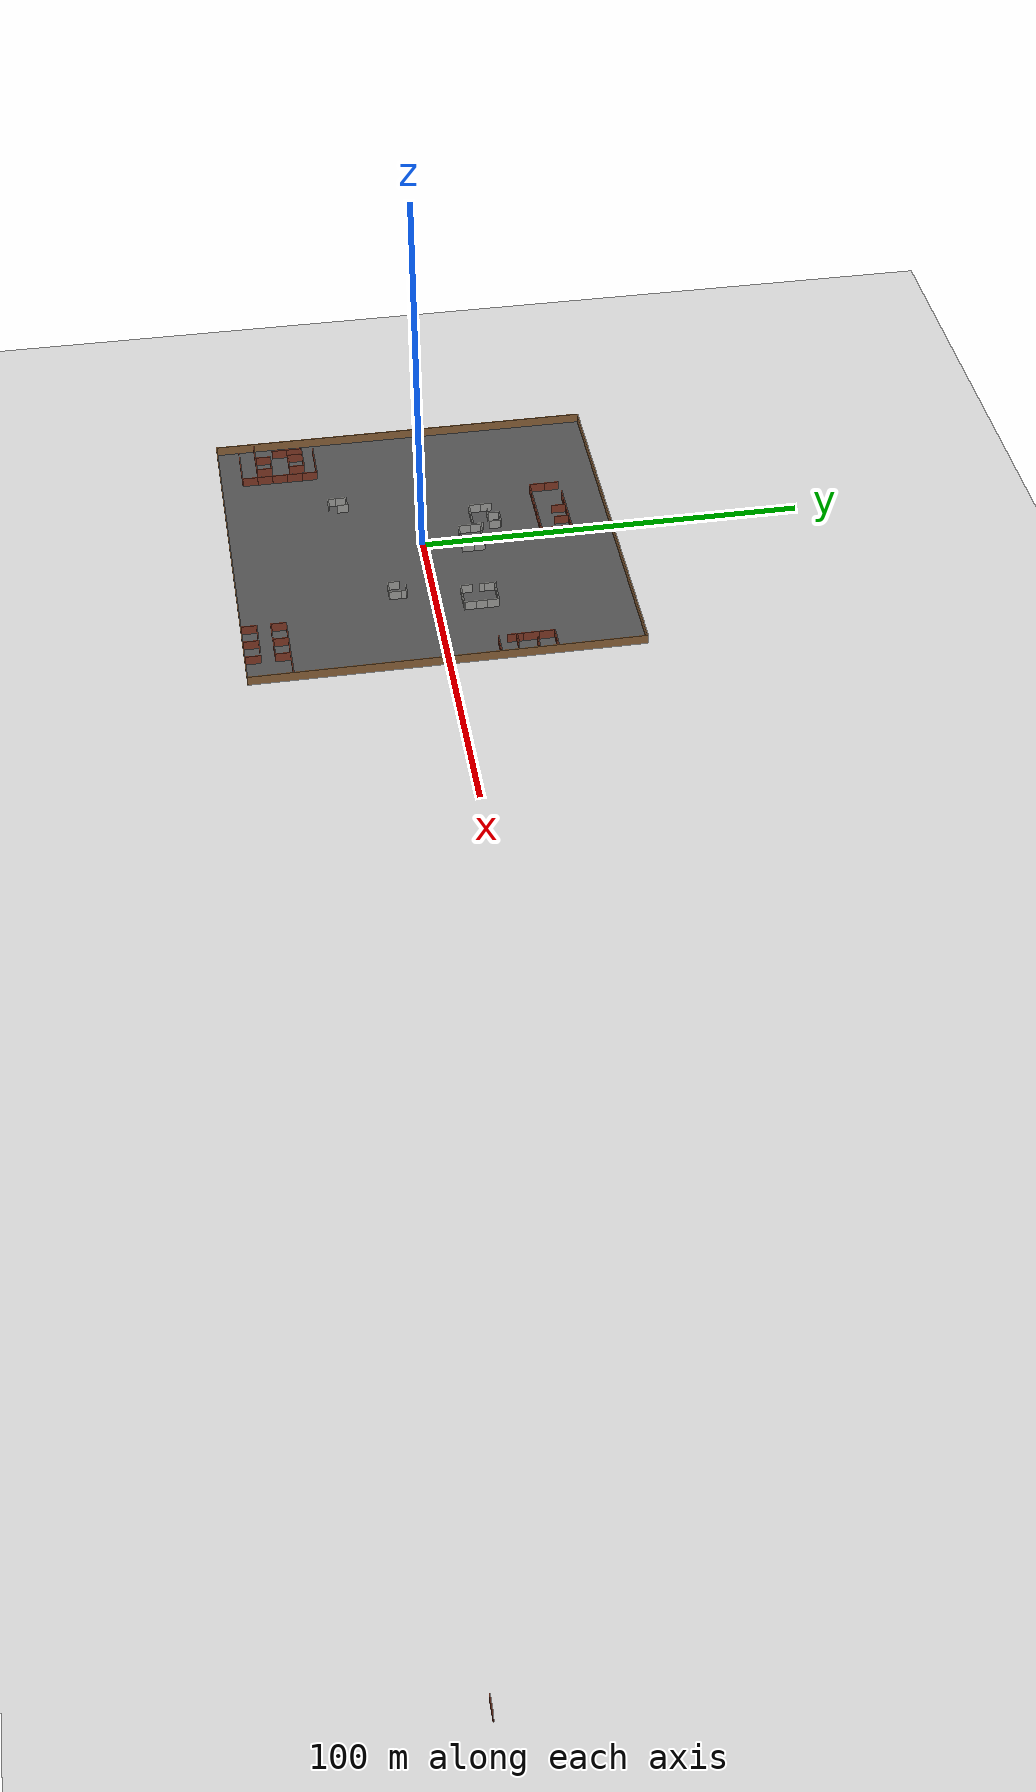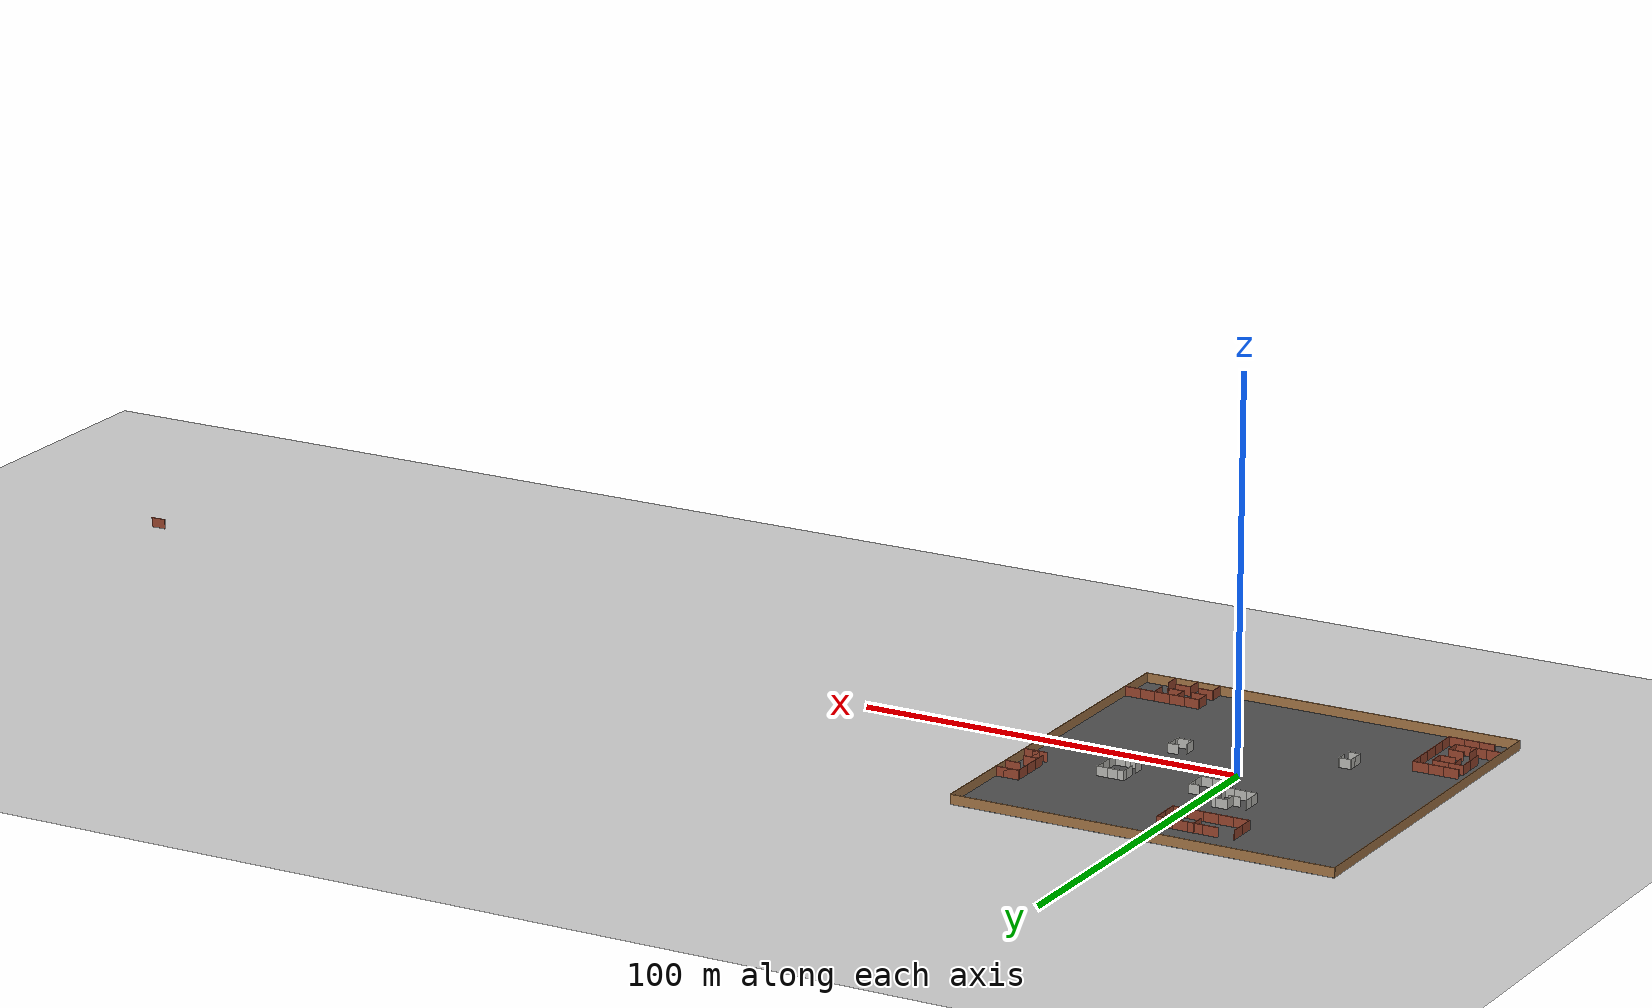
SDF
<sdf version="1.6">
 <world name="default">
  <light name="sun" type="directional">
   <pose>0 0 10 0 -0 0</pose>
   <diffuse>0.8 0.8 0.8 1</diffuse>
   <specular>0.2 0.2 0.2 1</specular>
   <attenuation>
    <range>1000</range>
    <constant>0.9</constant>
    <linear>0.01</linear>
    <quadratic>0.001</quadratic>
   </attenuation>
   <direction>-0.5 0.1 -0.9</direction>
  </light>
  <model name="ground_plane">
   <static>1</static>
   <link name="link">
    <collision name="collision">
     <geometry><plane><normal>0 0 1</normal><size>100 100</size></plane></geometry>
     <surface><friction><ode><mu>100</mu><mu2>50</mu2></ode></friction></surface>
    </collision>
    <visual name="visual">
     <cast_shadows>0</cast_shadows>
     <geometry><plane><normal>0 0 1</normal><size>100 100</size></plane></geometry>
     <material>
      <script><uri>file://media/materials/scripts/gazebo.material</uri><name>Gazebo/Grey</name></script>
     </material>
    </visual>
   </link>
  </model>
  <gravity>0 0 -9.8</gravity>
  <plugin name="gazebo_simple_world" filename="libgazebo_simple_world.so"/>
  <magnetic_field>6e-06 2.3e-05 -4.2e-05</magnetic_field>
  <atmosphere type="adiabatic"/>
  <physics name="default_physics" default="0" type="ode">
   <max_step_size>0.001</max_step_size>
   <real_time_factor>1</real_time_factor>
   <real_time_update_rate>1000</real_time_update_rate>
  </physics>
  <scene><ambient>0.4 0.4 0.4 1</ambient><background>0.7 0.7 0.7 1</background><shadows>1</shadows></scene>
  <audio><device>default</device></audio>
  <spherical_coordinates>
   <surface_model>EARTH_WGS84</surface_model>
   <latitude_deg>0</latitude_deg>
   <longitude_deg>0</longitude_deg>
   <elevation>0</elevation>
   <heading_deg>0</heading_deg>
  </spherical_coordinates>
  <model name="map_frame">
   <link name="Wall_0">
    <collision name="Wall_0_Collision">
     <geometry><box><size>100.05 0.15 2.5</size></box></geometry>
     <pose>0 0 1.25 0 -0 0</pose>
    </collision>
    <visual name="Wall_0_Visual">
     <pose>0 0 1.25 0 -0 0</pose>
     <geometry><box><size>100.05 0.15 2.5</size></box></geometry>
     <material>
      <script><uri>file://media/materials/scripts/gazebo.material</uri><name>Gazebo/Wood</name></script>
      <ambient>1 1 1 1</ambient>
     </material>
    </visual>
    <pose>0 50 0 0 -0 0</pose>
   </link>
   <link name="Wall_1">
    <collision name="Wall_1_Collision">
     <geometry><box><size>100.05 0.15 2.5</size></box></geometry>
     <pose>0 0 1.25 0 -0 0</pose>
    </collision>
    <visual name="Wall_1_Visual">
     <pose>0 0 1.25 0 -0 0</pose>
     <geometry><box><size>100.05 0.15 2.5</size></box></geometry>
     <material>
      <script><uri>file://media/materials/scripts/gazebo.material</uri><name>Gazebo/Wood</name></script>
      <ambient>1 1 1 1</ambient>
     </material>
    </visual>
    <pose>50 0 0 0 0 -1.5708</pose>
   </link>
   <link name="Wall_2">
    <collision name="Wall_2_Collision">
     <geometry><box><size>100.05 0.15 2.5</size></box></geometry>
     <pose>0 0 1.25 0 -0 0</pose>
    </collision>
    <visual name="Wall_2_Visual">
     <pose>0 0 1.25 0 -0 0</pose>
     <geometry><box><size>100.05 0.15 2.5</size></box></geometry>
     <material>
      <script><uri>file://media/materials/scripts/gazebo.material</uri><name>Gazebo/Wood</name></script>
      <ambient>1 1 1 1</ambient>
     </material>
    </visual>
    <pose>0 -50 0 0 -0 3.14159</pose>
   </link>
   <link name="Wall_3">
    <collision name="Wall_3_Collision">
     <geometry><box><size>100.05 0.15 2.5</size></box></geometry>
     <pose>0 0 1.25 0 -0 0</pose>
    </collision>
    <visual name="Wall_3_Visual">
     <pose>0 0 1.25 0 -0 0</pose>
     <geometry><box><size>100.05 0.15 2.5</size></box></geometry>
     <material>
      <script><uri>file://media/materials/scripts/gazebo.material</uri><name>Gazebo/Wood</name></script>
      <ambient>1 1 1 1</ambient>
     </material>
    </visual>
    <pose>-50 0 0 0 -0 1.5708</pose>
   </link>
   <static>1</static>
  </model>
  <model name="asphalt_plane">
   <static>1</static>
   <link name="link">
    <collision name="collision"><geometry><box><size>100 100 0.1</size></box></geometry></collision>
    <visual name="visual">
     <cast_shadows>0</cast_shadows>
     <geometry><box><size>100 100 0.1</size></box></geometry>
     <material>
      <script>
       <uri>model://asphalt_plane/materials/scripts</uri>
       <uri>model://asphalt_plane/materials/textures</uri>
       <name>vrc/asphalt</name>
      </script>
     </material>
    </visual>
   </link>
  </model>
  <model name="concrete_wall">
   <pose>-3.44413 14.4314 0 0 -0 0</pose>
   <link name="Wall_0">
    <collision name="Wall_0_Collision">
     <geometry><box><size>3 0.15 2.5</size></box></geometry>
     <pose>0 0 1.25 0 -0 0</pose>
    </collision>
    <visual name="Wall_0_Visual">
     <pose>0 0 1.25 0 -0 0</pose>
     <geometry><box><size>3 0.15 2.5</size></box></geometry>
     <material>
      <script><uri>file://media/materials/scripts/gazebo.material</uri><name>Gazebo/CeilingTiled</name></script>
      <ambient>1 1 1 1</ambient>
     </material>
     <meta><layer>0</layer></meta>
    </visual>
    <pose>0 0 0 0 -0 1.5708</pose>
   </link>
   <static>1</static>
  </model>
  <model name="concrete_wall_0">
   <pose>-3.44364 11.4407 0 0 -0 0</pose>
   <link name="Wall_0">
    <collision name="Wall_0_Collision">
     <geometry><box><size>3 0.15 2.5</size></box></geometry>
     <pose>0 0 1.25 0 -0 0</pose>
    </collision>
    <visual name="Wall_0_Visual">
     <pose>0 0 1.25 0 -0 0</pose>
     <geometry><box><size>3 0.15 2.5</size></box></geometry>
     <material>
      <script><uri>file://media/materials/scripts/gazebo.material</uri><name>Gazebo/CeilingTiled</name></script>
      <ambient>1 1 1 1</ambient>
     </material>
     <meta><layer>0</layer></meta>
    </visual>
    <pose>0 0 0 0 -0 1.5708</pose>
   </link>
   <static>1</static>
  </model>
  <model name="concrete_wall_1">
   <pose>4.66601 14.331 0 0 -0 0</pose>
   <link name="Wall_0">
    <collision name="Wall_0_Collision">
     <geometry><box><size>3 0.15 2.5</size></box></geometry>
     <pose>0 0 1.25 0 -0 0</pose>
    </collision>
    <visual name="Wall_0_Visual">
     <pose>0 0 1.25 0 -0 0</pose>
     <geometry><box><size>3 0.15 2.5</size></box></geometry>
     <material>
      <script><uri>file://media/materials/scripts/gazebo.material</uri><name>Gazebo/CeilingTiled</name></script>
      <ambient>1 1 1 1</ambient>
     </material>
     <meta><layer>0</layer></meta>
    </visual>
    <pose>0 0 0 0 -0 1.5708</pose>
   </link>
   <static>1</static>
  </model>
  <model name="concrete_wall_2">
   <pose>4.66901 11.3398 0 0 -0 0</pose>
   <link name="Wall_0">
    <collision name="Wall_0_Collision">
     <geometry><box><size>3 0.15 2.5</size></box></geometry>
     <pose>0 0 1.25 0 -0 0</pose>
    </collision>
    <visual name="Wall_0_Visual">
     <pose>0 0 1.25 0 -0 0</pose>
     <geometry><box><size>3 0.15 2.5</size></box></geometry>
     <material>
      <script><uri>file://media/materials/scripts/gazebo.material</uri><name>Gazebo/CeilingTiled</name></script>
      <ambient>1 1 1 1</ambient>
     </material>
     <meta><layer>0</layer></meta>
    </visual>
    <pose>0 0 0 0 -0 1.5708</pose>
   </link>
   <static>1</static>
  </model>
  <model name="concrete_wall_3">
   <pose>-21.066 -21.2152 0 0 -0 0</pose>
   <link name="Wall_0">
    <collision name="Wall_0_Collision">
     <geometry><box><size>3 0.15 2.5</size></box></geometry>
     <pose>0 0 1.25 0 -0 0</pose>
    </collision>
    <visual name="Wall_0_Visual">
     <pose>0 0 1.25 0 -0 0</pose>
     <geometry><box><size>3 0.15 2.5</size></box></geometry>
     <material>
      <script><uri>file://media/materials/scripts/gazebo.material</uri><name>Gazebo/CeilingTiled</name></script>
      <ambient>1 1 1 1</ambient>
     </material>
     <meta><layer>0</layer></meta>
    </visual>
    <pose>0 0 0 0 -0 1.5708</pose>
   </link>
   <static>1</static>
  </model>
  <model name="concrete_wall_4">
   <pose>-21.0568 -19.2132 0 0 -0 0</pose>
   <link name="Wall_0">
    <collision name="Wall_0_Collision">
     <geometry><box><size>3 0.15 2.5</size></box></geometry>
     <pose>0 0 1.25 0 -0 0</pose>
    </collision>
    <visual name="Wall_0_Visual">
     <pose>0 0 1.25 0 -0 0</pose>
     <geometry><box><size>3 0.15 2.5</size></box></geometry>
     <material>
      <script><uri>file://media/materials/scripts/gazebo.material</uri><name>Gazebo/CeilingTiled</name></script>
      <ambient>1 1 1 1</ambient>
     </material>
     <meta><layer>0</layer></meta>
    </visual>
    <pose>0 0 0 0 -0 1.5708</pose>
   </link>
   <static>1</static>
  </model>
  <model name="concrete_wall_5">
   <pose>-17.8818 -19.0275 0 0 -0 0</pose>
   <link name="Wall_0">
    <collision name="Wall_0_Collision">
     <geometry><box><size>3 0.15 2.5</size></box></geometry>
     <pose>0 0 1.25 0 -0 0</pose>
    </collision>
    <visual name="Wall_0_Visual">
     <pose>0 0 1.25 0 -0 0</pose>
     <geometry><box><size>3 0.15 2.5</size></box></geometry>
     <material>
      <script><uri>file://media/materials/scripts/gazebo.material</uri><name>Gazebo/CeilingTiled</name></script>
      <ambient>1 1 1 1</ambient>
     </material>
     <meta><layer>0</layer></meta>
    </visual>
    <pose>0 0 0 0 -0 1.5708</pose>
   </link>
   <static>1</static>
  </model>
  <model name="concrete_wall_6_clone">
   <pose>-19.5085 -22.6271 0 0 -0 1.57079</pose>
   <link name="Wall_0">
    <collision name="Wall_0_Collision">
     <geometry><box><size>3 0.15 2.5</size></box></geometry>
     <pose>0 0 1.25 0 -0 0</pose>
    </collision>
    <visual name="Wall_0_Visual">
     <pose>0 0 1.25 0 -0 0</pose>
     <geometry><box><size>3 0.15 2.5</size></box></geometry>
     <material>
      <script><uri>file://media/materials/scripts/gazebo.material</uri><name>Gazebo/CeilingTiled</name></script>
      <ambient>1 1 1 1</ambient>
     </material>
     <meta><layer>0</layer></meta>
    </visual>
    <pose>0 0 0 0 -0 1.5708</pose>
   </link>
   <static>1</static>
  </model>
  <model name="concrete_wall_6_clone_0">
   <pose>-19.4814 -17.8466 0 0 -0 1.57079</pose>
   <link name="Wall_0">
    <collision name="Wall_0_Collision">
     <geometry><box><size>3 0.15 2.5</size></box></geometry>
     <pose>0 0 1.25 0 -0 0</pose>
    </collision>
    <visual name="Wall_0_Visual">
     <pose>0 0 1.25 0 -0 0</pose>
     <geometry><box><size>3 0.15 2.5</size></box></geometry>
     <material>
      <script><uri>file://media/materials/scripts/gazebo.material</uri><name>Gazebo/CeilingTiled</name></script>
      <ambient>1 1 1 1</ambient>
     </material>
     <meta><layer>0</layer></meta>
    </visual>
    <pose>0 0 0 0 -0 1.5708</pose>
   </link>
   <static>1</static>
  </model>
  <model name="concrete_wall_6_clone_1">
   <pose>20.7484 -7.01357 0 0 -0 1.57079</pose>
   <link name="Wall_0">
    <collision name="Wall_0_Collision">
     <geometry><box><size>3 0.15 2.5</size></box></geometry>
     <pose>0 0 1.25 0 -0 0</pose>
    </collision>
    <visual name="Wall_0_Visual">
     <pose>0 0 1.25 0 -0 0</pose>
     <geometry><box><size>3 0.15 2.5</size></box></geometry>
     <material>
      <script><uri>file://media/materials/scripts/gazebo.material</uri><name>Gazebo/CeilingTiled</name></script>
      <ambient>1 1 1 1</ambient>
     </material>
     <meta><layer>0</layer></meta>
    </visual>
    <pose>0 0 0 0 -0 1.5708</pose>
   </link>
   <static>1</static>
  </model>
  <model name="concrete_wall_6_clone_2">
   <pose>20.3039 -11.4446 0 0 -0 1.57079</pose>
   <link name="Wall_0">
    <collision name="Wall_0_Collision">
     <geometry><box><size>3 0.15 2.5</size></box></geometry>
     <pose>0 0 1.25 0 -0 0</pose>
    </collision>
    <visual name="Wall_0_Visual">
     <pose>0 0 1.25 0 -0 0</pose>
     <geometry><box><size>3 0.15 2.5</size></box></geometry>
     <material>
      <script><uri>file://media/materials/scripts/gazebo.material</uri><name>Gazebo/CeilingTiled</name></script>
      <ambient>1 1 1 1</ambient>
     </material>
     <meta><layer>0</layer></meta>
    </visual>
    <pose>0 0 0 0 -0 1.5708</pose>
   </link>
   <static>1</static>
  </model>
  <model name="concrete_wall_6_clone_3">
   <pose>19.1368 -11.4558 0 0 -0 1.57079</pose>
   <link name="Wall_0">
    <collision name="Wall_0_Collision">
     <geometry><box><size>3 0.15 2.5</size></box></geometry>
     <pose>0 0 1.25 0 -0 0</pose>
    </collision>
    <visual name="Wall_0_Visual">
     <pose>0 0 1.25 0 -0 0</pose>
     <geometry><box><size>3 0.15 2.5</size></box></geometry>
     <material>
      <script><uri>file://media/materials/scripts/gazebo.material</uri><name>Gazebo/CeilingTiled</name></script>
      <ambient>1 1 1 1</ambient>
     </material>
     <meta><layer>0</layer></meta>
    </visual>
    <pose>0 0 0 0 -0 1.5708</pose>
   </link>
   <static>1</static>
  </model>
  <model name="concrete_wall_7">
   <pose>17.7318 -9.91545 0 0 -0 0</pose>
   <link name="Wall_0">
    <collision name="Wall_0_Collision">
     <geometry><box><size>3 0.15 2.5</size></box></geometry>
     <pose>0 0 1.25 0 -0 0</pose>
    </collision>
    <visual name="Wall_0_Visual">
     <pose>0 0 1.25 0 -0 0</pose>
     <geometry><box><size>3 0.15 2.5</size></box></geometry>
     <material>
      <script><uri>file://media/materials/scripts/gazebo.material</uri><name>Gazebo/CeilingTiled</name></script>
      <ambient>1 1 1 1</ambient>
     </material>
     <meta><layer>0</layer></meta>
    </visual>
    <pose>0 0 0 0 -0 1.5708</pose>
   </link>
   <static>1</static>
  </model>
  <model name="concrete_wall_8">
   <pose>21.7794 -9.93205 0 0 -0 0</pose>
   <link name="Wall_0">
    <collision name="Wall_0_Collision">
     <geometry><box><size>3 0.15 2.5</size></box></geometry>
     <pose>0 0 1.25 0 -0 0</pose>
    </collision>
    <visual name="Wall_0_Visual">
     <pose>0 0 1.25 0 -0 0</pose>
     <geometry><box><size>3 0.15 2.5</size></box></geometry>
     <material>
      <script><uri>file://media/materials/scripts/gazebo.material</uri><name>Gazebo/CeilingTiled</name></script>
      <ambient>1 1 1 1</ambient>
     </material>
     <meta><layer>0</layer></meta>
    </visual>
    <pose>0 0 0 0 -0 1.5708</pose>
   </link>
   <static>1</static>
  </model>
  <model name="concrete_wall_9">
   <pose>21.7635 -8.54711 0 0 -0 0</pose>
   <link name="Wall_0">
    <collision name="Wall_0_Collision">
     <geometry><box><size>3 0.15 2.5</size></box></geometry>
     <pose>0 0 1.25 0 -0 0</pose>
    </collision>
    <visual name="Wall_0_Visual">
     <pose>0 0 1.25 0 -0 0</pose>
     <geometry><box><size>3 0.15 2.5</size></box></geometry>
     <material>
      <script><uri>file://media/materials/scripts/gazebo.material</uri><name>Gazebo/CeilingTiled</name></script>
      <ambient>1 1 1 1</ambient>
     </material>
     <meta><layer>0</layer></meta>
    </visual>
    <pose>0 0 0 0 -0 1.5708</pose>
   </link>
   <static>1</static>
  </model>
  <model name="concrete_wall_6_clone_4">
   <pose>3.13686 9.88392 0 0 -0 1.57079</pose>
   <link name="Wall_0">
    <collision name="Wall_0_Collision">
     <geometry><box><size>3 0.15 2.5</size></box></geometry>
     <pose>0 0 1.25 0 -0 0</pose>
    </collision>
    <visual name="Wall_0_Visual">
     <pose>0 0 1.25 0 -0 0</pose>
     <geometry><box><size>3 0.15 2.5</size></box></geometry>
     <material>
      <script><uri>file://media/materials/scripts/gazebo.material</uri><name>Gazebo/CeilingTiled</name></script>
      <ambient>1 1 1 1</ambient>
     </material>
     <meta><layer>0</layer></meta>
    </visual>
    <pose>0 0 0 0 -0 1.5708</pose>
   </link>
   <static>1</static>
  </model>
  <model name="concrete_wall_6_clone_5">
   <pose>0.16157 9.88256 0 0 -0 1.57079</pose>
   <link name="Wall_0">
    <collision name="Wall_0_Collision">
     <geometry><box><size>3 0.15 2.5</size></box></geometry>
     <pose>0 0 1.25 0 -0 0</pose>
    </collision>
    <visual name="Wall_0_Visual">
     <pose>0 0 1.25 0 -0 0</pose>
     <geometry><box><size>3 0.15 2.5</size></box></geometry>
     <material>
      <script><uri>file://media/materials/scripts/gazebo.material</uri><name>Gazebo/CeilingTiled</name></script>
      <ambient>1 1 1 1</ambient>
     </material>
     <meta><layer>0</layer></meta>
    </visual>
    <pose>0 0 0 0 -0 1.5708</pose>
   </link>
   <static>1</static>
  </model>
  <model name="concrete_wall_6_clone_6">
   <pose>-1.99874 9.88847 0 0 -0 1.57079</pose>
   <link name="Wall_0">
    <collision name="Wall_0_Collision">
     <geometry><box><size>3 0.15 2.5</size></box></geometry>
     <pose>0 0 1.25 0 -0 0</pose>
    </collision>
    <visual name="Wall_0_Visual">
     <pose>0 0 1.25 0 -0 0</pose>
     <geometry><box><size>3 0.15 2.5</size></box></geometry>
     <material>
      <script><uri>file://media/materials/scripts/gazebo.material</uri><name>Gazebo/CeilingTiled</name></script>
      <ambient>1 1 1 1</ambient>
     </material>
     <meta><layer>0</layer></meta>
    </visual>
    <pose>0 0 0 0 -0 1.5708</pose>
   </link>
   <static>1</static>
  </model>
  <model name="concrete_wall_6_clone_7">
   <pose>-1.94158 15.788 0 0 -0 1.57079</pose>
   <link name="Wall_0">
    <collision name="Wall_0_Collision">
     <geometry><box><size>3 0.15 2.5</size></box></geometry>
     <pose>0 0 1.25 0 -0 0</pose>
    </collision>
    <visual name="Wall_0_Visual">
     <pose>0 0 1.25 0 -0 0</pose>
     <geometry><box><size>3 0.15 2.5</size></box></geometry>
     <material>
      <script><uri>file://media/materials/scripts/gazebo.material</uri><name>Gazebo/CeilingTiled</name></script>
      <ambient>1 1 1 1</ambient>
     </material>
     <meta><layer>0</layer></meta>
    </visual>
    <pose>0 0 0 0 -0 1.5708</pose>
   </link>
   <static>1</static>
  </model>
  <model name="concrete_wall_6_clone_8">
   <pose>3.56787 15.7539 0 0 -0 1.57079</pose>
   <link name="Wall_0">
    <collision name="Wall_0_Collision">
     <geometry><box><size>3 0.15 2.5</size></box></geometry>
     <pose>0 0 1.25 0 -0 0</pose>
    </collision>
    <visual name="Wall_0_Visual">
     <pose>0 0 1.25 0 -0 0</pose>
     <geometry><box><size>3 0.15 2.5</size></box></geometry>
     <material>
      <script><uri>file://media/materials/scripts/gazebo.material</uri><name>Gazebo/CeilingTiled</name></script>
      <ambient>1 1 1 1</ambient>
     </material>
     <meta><layer>0</layer></meta>
    </visual>
    <pose>0 0 0 0 -0 1.5708</pose>
   </link>
   <static>1</static>
  </model>
  <model name="concrete_wall_6_clone_9">
   <pose>-10.7665 13.9394 0 0 -0 1.57079</pose>
   <link name="Wall_0">
    <collision name="Wall_0_Collision">
     <geometry><box><size>3 0.15 2.5</size></box></geometry>
     <pose>0 0 1.25 0 -0 0</pose>
    </collision>
    <visual name="Wall_0_Visual">
     <pose>0 0 1.25 0 -0 0</pose>
     <geometry><box><size>3 0.15 2.5</size></box></geometry>
     <material>
      <script><uri>file://media/materials/scripts/gazebo.material</uri><name>Gazebo/CeilingTiled</name></script>
      <ambient>1 1 1 1</ambient>
     </material>
     <meta><layer>0</layer></meta>
    </visual>
    <pose>0 0 0 0 -0 1.5708</pose>
   </link>
   <static>1</static>
  </model>
  <model name="concrete_wall_6_clone_10">
   <pose>-7.79777 13.9437 0 0 -0 1.57079</pose>
   <link name="Wall_0">
    <collision name="Wall_0_Collision">
     <geometry><box><size>3 0.15 2.5</size></box></geometry>
     <pose>0 0 1.25 0 -0 0</pose>
    </collision>
    <visual name="Wall_0_Visual">
     <pose>0 0 1.25 0 -0 0</pose>
     <geometry><box><size>3 0.15 2.5</size></box></geometry>
     <material>
      <script><uri>file://media/materials/scripts/gazebo.material</uri><name>Gazebo/CeilingTiled</name></script>
      <ambient>1 1 1 1</ambient>
     </material>
     <meta><layer>0</layer></meta>
    </visual>
    <pose>0 0 0 0 -0 1.5708</pose>
   </link>
   <static>1</static>
  </model>
  <model name="concrete_wall_6_clone_11">
   <pose>-5.01284 13.934 0 0 -0 1.57079</pose>
   <link name="Wall_0">
    <collision name="Wall_0_Collision">
     <geometry><box><size>3 0.15 2.5</size></box></geometry>
     <pose>0 0 1.25 0 -0 0</pose>
    </collision>
    <visual name="Wall_0_Visual">
     <pose>0 0 1.25 0 -0 0</pose>
     <geometry><box><size>3 0.15 2.5</size></box></geometry>
     <material>
      <script><uri>file://media/materials/scripts/gazebo.material</uri><name>Gazebo/CeilingTiled</name></script>
      <ambient>1 1 1 1</ambient>
     </material>
     <meta><layer>0</layer></meta>
    </visual>
    <pose>0 0 0 0 -0 1.5708</pose>
   </link>
   <static>1</static>
  </model>
  <model name="concrete_wall_6_clone_12">
   <pose>-6.55197 21.3742 0 0 -0 1.57079</pose>
   <link name="Wall_0">
    <collision name="Wall_0_Collision">
     <geometry><box><size>3 0.15 2.5</size></box></geometry>
     <pose>0 0 1.25 0 -0 0</pose>
    </collision>
    <visual name="Wall_0_Visual">
     <pose>0 0 1.25 0 -0 0</pose>
     <geometry><box><size>3 0.15 2.5</size></box></geometry>
     <material>
      <script><uri>file://media/materials/scripts/gazebo.material</uri><name>Gazebo/CeilingTiled</name></script>
      <ambient>1 1 1 1</ambient>
     </material>
     <meta><layer>0</layer></meta>
    </visual>
    <pose>0 0 0 0 -0 1.5708</pose>
   </link>
   <static>1</static>
  </model>
  <model name="concrete_wall_6_clone_13">
   <pose>-5.53068 21.3667 0 0 -0 1.57079</pose>
   <link name="Wall_0">
    <collision name="Wall_0_Collision">
     <geometry><box><size>3 0.15 2.5</size></box></geometry>
     <pose>0 0 1.25 0 -0 0</pose>
    </collision>
    <visual name="Wall_0_Visual">
     <pose>0 0 1.25 0 -0 0</pose>
     <geometry><box><size>3 0.15 2.5</size></box></geometry>
     <material>
      <script><uri>file://media/materials/scripts/gazebo.material</uri><name>Gazebo/CeilingTiled</name></script>
      <ambient>1 1 1 1</ambient>
     </material>
     <meta><layer>0</layer></meta>
    </visual>
    <pose>0 0 0 0 -0 1.5708</pose>
   </link>
   <static>1</static>
  </model>
  <model name="concrete_wall_10">
   <pose>-12.1983 15.5037 0 0 -0 0</pose>
   <link name="Wall_0">
    <collision name="Wall_0_Collision">
     <geometry><box><size>3 0.15 2.5</size></box></geometry>
     <pose>0 0 1.25 0 -0 0</pose>
    </collision>
    <visual name="Wall_0_Visual">
     <pose>0 0 1.25 0 -0 0</pose>
     <geometry><box><size>3 0.15 2.5</size></box></geometry>
     <material>
      <script><uri>file://media/materials/scripts/gazebo.material</uri><name>Gazebo/CeilingTiled</name></script>
      <ambient>1 1 1 1</ambient>
     </material>
     <meta><layer>0</layer></meta>
    </visual>
    <pose>0 0 0 0 -0 1.5708</pose>
   </link>
   <static>1</static>
  </model>
  <model name="concrete_wall_11">
   <pose>-12.197 18.4288 0 0 -0 0</pose>
   <link name="Wall_0">
    <collision name="Wall_0_Collision">
     <geometry><box><size>3 0.15 2.5</size></box></geometry>
     <pose>0 0 1.25 0 -0 0</pose>
    </collision>
    <visual name="Wall_0_Visual">
     <pose>0 0 1.25 0 -0 0</pose>
     <geometry><box><size>3 0.15 2.5</size></box></geometry>
     <material>
      <script><uri>file://media/materials/scripts/gazebo.material</uri><name>Gazebo/CeilingTiled</name></script>
      <ambient>1 1 1 1</ambient>
     </material>
     <meta><layer>0</layer></meta>
    </visual>
    <pose>0 0 0 0 -0 1.5708</pose>
   </link>
   <static>1</static>
  </model>
  <model name="concrete_wall_12">
   <pose>-4.28143 19.8004 0 0 -0 0</pose>
   <link name="Wall_0">
    <collision name="Wall_0_Collision">
     <geometry><box><size>3 0.15 2.5</size></box></geometry>
     <pose>0 0 1.25 0 -0 0</pose>
    </collision>
    <visual name="Wall_0_Visual">
     <pose>0 0 1.25 0 -0 0</pose>
     <geometry><box><size>3 0.15 2.5</size></box></geometry>
     <material>
      <script><uri>file://media/materials/scripts/gazebo.material</uri><name>Gazebo/CeilingTiled</name></script>
      <ambient>1 1 1 1</ambient>
     </material>
     <meta><layer>0</layer></meta>
    </visual>
    <pose>0 0 0 0 -0 1.5708</pose>
   </link>
   <static>1</static>
  </model>
  <model name="concrete_wall_13">
   <pose>-3.86438 15.0004 0 0 -0 0</pose>
   <link name="Wall_0">
    <collision name="Wall_0_Collision">
     <geometry><box><size>3 0.15 2.5</size></box></geometry>
     <pose>0 0 1.25 0 -0 0</pose>
    </collision>
    <visual name="Wall_0_Visual">
     <pose>0 0 1.25 0 -0 0</pose>
     <geometry><box><size>3 0.15 2.5</size></box></geometry>
     <material>
      <script><uri>file://media/materials/scripts/gazebo.material</uri><name>Gazebo/CeilingTiled</name></script>
      <ambient>1 1 1 1</ambient>
     </material>
     <meta><layer>0</layer></meta>
    </visual>
    <pose>0 0 0 0 -0 1.5708</pose>
   </link>
   <static>1</static>
  </model>
  <model name="concrete_wall_14">
   <pose>-8.00651 19.8559 0 0 -0 0</pose>
   <link name="Wall_0">
    <collision name="Wall_0_Collision">
     <geometry><box><size>3 0.15 2.5</size></box></geometry>
     <pose>0 0 1.25 0 -0 0</pose>
    </collision>
    <visual name="Wall_0_Visual">
     <pose>0 0 1.25 0 -0 0</pose>
     <geometry><box><size>3 0.15 2.5</size></box></geometry>
     <material>
      <script><uri>file://media/materials/scripts/gazebo.material</uri><name>Gazebo/CeilingTiled</name></script>
      <ambient>1 1 1 1</ambient>
     </material>
     <meta><layer>0</layer></meta>
    </visual>
    <pose>0 0 0 0 -0 1.5708</pose>
   </link>
   <static>1</static>
  </model>
  <model name="concrete_wall_6_clone_14">
   <pose>-8.44061 18.3913 0 0 -0 1.57079</pose>
   <link name="Wall_0">
    <collision name="Wall_0_Collision">
     <geometry><box><size>3 0.15 2.5</size></box></geometry>
     <pose>0 0 1.25 0 -0 0</pose>
    </collision>
    <visual name="Wall_0_Visual">
     <pose>0 0 1.25 0 -0 0</pose>
     <geometry><box><size>3 0.15 2.5</size></box></geometry>
     <material>
      <script><uri>file://media/materials/scripts/gazebo.material</uri><name>Gazebo/CeilingTiled</name></script>
      <ambient>1 1 1 1</ambient>
     </material>
     <meta><layer>0</layer></meta>
    </visual>
    <pose>0 0 0 0 -0 1.5708</pose>
   </link>
   <static>1</static>
  </model>
  <model name="concrete_wall_6_clone_15">
   <pose>23.534 6.78202 0 0 -0 1.57079</pose>
   <link name="Wall_0">
    <collision name="Wall_0_Collision">
     <geometry><box><size>3 0.15 2.5</size></box></geometry>
     <pose>0 0 1.25 0 -0 0</pose>
    </collision>
    <visual name="Wall_0_Visual">
     <pose>0 0 1.25 0 -0 0</pose>
     <geometry><box><size>3 0.15 2.5</size></box></geometry>
     <material>
      <script><uri>file://media/materials/scripts/gazebo.material</uri><name>Gazebo/CeilingTiled</name></script>
      <ambient>1 1 1 1</ambient>
     </material>
     <meta><layer>0</layer></meta>
    </visual>
    <pose>0 0 0 0 -0 1.5708</pose>
   </link>
   <static>1</static>
  </model>
  <model name="concrete_wall_6_clone_16">
   <pose>25.863 6.76889 0 0 -0 1.57079</pose>
   <link name="Wall_0">
    <collision name="Wall_0_Collision">
     <geometry><box><size>3 0.15 2.5</size></box></geometry>
     <pose>0 0 1.25 0 -0 0</pose>
    </collision>
    <visual name="Wall_0_Visual">
     <pose>0 0 1.25 0 -0 0</pose>
     <geometry><box><size>3 0.15 2.5</size></box></geometry>
     <material>
      <script><uri>file://media/materials/scripts/gazebo.material</uri><name>Gazebo/CeilingTiled</name></script>
      <ambient>1 1 1 1</ambient>
     </material>
     <meta><layer>0</layer></meta>
    </visual>
    <pose>0 0 0 0 -0 1.5708</pose>
   </link>
   <static>1</static>
  </model>
  <model name="concrete_wall_6_clone_17">
   <pose>27.7288 6.77605 0 0 -0 1.57079</pose>
   <link name="Wall_0">
    <collision name="Wall_0_Collision">
     <geometry><box><size>3 0.15 2.5</size></box></geometry>
     <pose>0 0 1.25 0 -0 0</pose>
    </collision>
    <visual name="Wall_0_Visual">
     <pose>0 0 1.25 0 -0 0</pose>
     <geometry><box><size>3 0.15 2.5</size></box></geometry>
     <material>
      <script><uri>file://media/materials/scripts/gazebo.material</uri><name>Gazebo/CeilingTiled</name></script>
      <ambient>1 1 1 1</ambient>
     </material>
     <meta><layer>0</layer></meta>
    </visual>
    <pose>0 0 0 0 -0 1.5708</pose>
   </link>
   <static>1</static>
  </model>
  <model name="concrete_wall_6_clone_18">
   <pose>27.9453 15.6632 0 0 -0 1.57079</pose>
   <link name="Wall_0">
    <collision name="Wall_0_Collision">
     <geometry><box><size>3 0.15 2.5</size></box></geometry>
     <pose>0 0 1.25 0 -0 0</pose>
    </collision>
    <visual name="Wall_0_Visual">
     <pose>0 0 1.25 0 -0 0</pose>
     <geometry><box><size>3 0.15 2.5</size></box></geometry>
     <material>
      <script><uri>file://media/materials/scripts/gazebo.material</uri><name>Gazebo/CeilingTiled</name></script>
      <ambient>1 1 1 1</ambient>
     </material>
     <meta><layer>0</layer></meta>
    </visual>
    <pose>0 0 0 0 -0 1.5708</pose>
   </link>
   <static>1</static>
  </model>
  <model name="concrete_wall_6_clone_19">
   <pose>25.3933 15.6522 0 0 -0 1.57079</pose>
   <link name="Wall_0">
    <collision name="Wall_0_Collision">
     <geometry><box><size>3 0.15 2.5</size></box></geometry>
     <pose>0 0 1.25 0 -0 0</pose>
    </collision>
    <visual name="Wall_0_Visual">
     <pose>0 0 1.25 0 -0 0</pose>
     <geometry><box><size>3 0.15 2.5</size></box></geometry>
     <material>
      <script><uri>file://media/materials/scripts/gazebo.material</uri><name>Gazebo/CeilingTiled</name></script>
      <ambient>1 1 1 1</ambient>
     </material>
     <meta><layer>0</layer></meta>
    </visual>
    <pose>0 0 0 0 -0 1.5708</pose>
   </link>
   <static>1</static>
  </model>
  <model name="concrete_wall_6_clone_20">
   <pose>23.696 15.6424 0 0 -0 1.57079</pose>
   <link name="Wall_0">
    <collision name="Wall_0_Collision">
     <geometry><box><size>3 0.15 2.5</size></box></geometry>
     <pose>0 0 1.25 0 -0 0</pose>
    </collision>
    <visual name="Wall_0_Visual">
     <pose>0 0 1.25 0 -0 0</pose>
     <geometry><box><size>3 0.15 2.5</size></box></geometry>
     <material>
      <script><uri>file://media/materials/scripts/gazebo.material</uri><name>Gazebo/CeilingTiled</name></script>
      <ambient>1 1 1 1</ambient>
     </material>
     <meta><layer>0</layer></meta>
    </visual>
    <pose>0 0 0 0 -0 1.5708</pose>
   </link>
   <static>1</static>
  </model>
  <model name="concrete_wall_15">
   <pose>29.0909 8.30314 0 0 -0 0</pose>
   <link name="Wall_0">
    <collision name="Wall_0_Collision">
     <geometry><box><size>3 0.15 2.5</size></box></geometry>
     <pose>0 0 1.25 0 -0 0</pose>
    </collision>
    <visual name="Wall_0_Visual">
     <pose>0 0 1.25 0 -0 0</pose>
     <geometry><box><size>3 0.15 2.5</size></box></geometry>
     <material>
      <script><uri>file://media/materials/scripts/gazebo.material</uri><name>Gazebo/CeilingTiled</name></script>
      <ambient>1 1 1 1</ambient>
     </material>
     <meta><layer>0</layer></meta>
    </visual>
    <pose>0 0 0 0 -0 1.5708</pose>
   </link>
   <static>1</static>
  </model>
  <model name="concrete_wall_16">
   <pose>22.1252 8.21838 0 0 -0 0</pose>
   <link name="Wall_0">
    <collision name="Wall_0_Collision">
     <geometry><box><size>3 0.15 2.5</size></box></geometry>
     <pose>0 0 1.25 0 -0 0</pose>
    </collision>
    <visual name="Wall_0_Visual">
     <pose>0 0 1.25 0 -0 0</pose>
     <geometry><box><size>3 0.15 2.5</size></box></geometry>
     <material>
      <script><uri>file://media/materials/scripts/gazebo.material</uri><name>Gazebo/CeilingTiled</name></script>
      <ambient>1 1 1 1</ambient>
     </material>
     <meta><layer>0</layer></meta>
    </visual>
    <pose>0 0 0 0 -0 1.5708</pose>
   </link>
   <static>1</static>
  </model>
  <model name="concrete_wall_17">
   <pose>22.1327 13.047 0 0 -0 0</pose>
   <link name="Wall_0">
    <collision name="Wall_0_Collision">
     <geometry><box><size>3 0.15 2.5</size></box></geometry>
     <pose>0 0 1.25 0 -0 0</pose>
    </collision>
    <visual name="Wall_0_Visual">
     <pose>0 0 1.25 0 -0 0</pose>
     <geometry><box><size>3 0.15 2.5</size></box></geometry>
     <material>
      <script><uri>file://media/materials/scripts/gazebo.material</uri><name>Gazebo/CeilingTiled</name></script>
      <ambient>1 1 1 1</ambient>
     </material>
     <meta><layer>0</layer></meta>
    </visual>
    <pose>0 0 0 0 -0 1.5708</pose>
   </link>
   <static>1</static>
  </model>
  <model name="concrete_wall_18">
   <pose>22.1412 14.4159 0 0 -0 0</pose>
   <link name="Wall_0">
    <collision name="Wall_0_Collision">
     <geometry><box><size>3 0.15 2.5</size></box></geometry>
     <pose>0 0 1.25 0 -0 0</pose>
    </collision>
    <visual name="Wall_0_Visual">
     <pose>0 0 1.25 0 -0 0</pose>
     <geometry><box><size>3 0.15 2.5</size></box></geometry>
     <material>
      <script><uri>file://media/materials/scripts/gazebo.material</uri><name>Gazebo/CeilingTiled</name></script>
      <ambient>1 1 1 1</ambient>
     </material>
     <meta><layer>0</layer></meta>
    </visual>
    <pose>0 0 0 0 -0 1.5708</pose>
   </link>
   <static>1</static>
  </model>
  <model name="concrete_wall_19">
   <pose>29.1035 11.247 0 0 -0 0</pose>
   <link name="Wall_0">
    <collision name="Wall_0_Collision">
     <geometry><box><size>3 0.15 2.5</size></box></geometry>
     <pose>0 0 1.25 0 -0 0</pose>
    </collision>
    <visual name="Wall_0_Visual">
     <pose>0 0 1.25 0 -0 0</pose>
     <geometry><box><size>3 0.15 2.5</size></box></geometry>
     <material>
      <script><uri>file://media/materials/scripts/gazebo.material</uri><name>Gazebo/CeilingTiled</name></script>
      <ambient>1 1 1 1</ambient>
     </material>
     <meta><layer>0</layer></meta>
    </visual>
    <pose>0 0 0 0 -0 1.5708</pose>
   </link>
   <static>1</static>
  </model>
  <model name="concrete_wall_20">
   <pose>29.1055 14.1527 0 0 -0 0</pose>
   <link name="Wall_0">
    <collision name="Wall_0_Collision">
     <geometry><box><size>3 0.15 2.5</size></box></geometry>
     <pose>0 0 1.25 0 -0 0</pose>
    </collision>
    <visual name="Wall_0_Visual">
     <pose>0 0 1.25 0 -0 0</pose>
     <geometry><box><size>3 0.15 2.5</size></box></geometry>
     <material>
      <script><uri>file://media/materials/scripts/gazebo.material</uri><name>Gazebo/CeilingTiled</name></script>
      <ambient>1 1 1 1</ambient>
     </material>
     <meta><layer>0</layer></meta>
    </visual>
    <pose>0 0 0 0 -0 1.5708</pose>
   </link>
   <static>1</static>
  </model>
  <model name="brick_wall">
   <pose>47.9451 -38.5658 0 0 -0 0</pose>
   <link name="Wall_0">
    <collision name="Wall_0_Collision">
     <geometry><box><size>4 0.15 2.5</size></box></geometry>
     <pose>0 0 1.25 0 -0 0</pose>
    </collision>
    <visual name="Wall_0_Visual">
     <pose>0 0 1.25 0 -0 0</pose>
     <geometry><box><size>4 0.15 2.5</size></box></geometry>
     <material>
      <script><uri>file://media/materials/scripts/gazebo.material</uri><name>Gazebo/Bricks</name></script>
      <ambient>1 1 1 1</ambient>
     </material>
     <meta><layer>0</layer></meta>
    </visual>
   </link>
   <static>1</static>
  </model>
  <model name="brick_wall_0">
   <pose>43.9451 -38.5658 0 0 -0 0</pose>
   <link name="Wall_0">
    <collision name="Wall_0_Collision">
     <geometry><box><size>4 0.15 2.5</size></box></geometry>
     <pose>0 0 1.25 0 -0 0</pose>
    </collision>
    <visual name="Wall_0_Visual">
     <pose>0 0 1.25 0 -0 0</pose>
     <geometry><box><size>4 0.15 2.5</size></box></geometry>
     <material>
      <script><uri>file://media/materials/scripts/gazebo.material</uri><name>Gazebo/Bricks</name></script>
      <ambient>1 1 1 1</ambient>
     </material>
     <meta><layer>0</layer></meta>
    </visual>
   </link>
   <static>1</static>
  </model>
  <model name="brick_wall_clone">
   <pose>39.9451 -38.5658 0 0 -0 0</pose>
   <link name="Wall_0">
    <collision name="Wall_0_Collision">
     <geometry><box><size>4 0.15 2.5</size></box></geometry>
     <pose>0 0 1.25 0 -0 0</pose>
    </collision>
    <visual name="Wall_0_Visual">
     <pose>0 0 1.25 0 -0 0</pose>
     <geometry><box><size>4 0.15 2.5</size></box></geometry>
     <material>
      <script><uri>file://media/materials/scripts/gazebo.material</uri><name>Gazebo/Bricks</name></script>
      <ambient>1 1 1 1</ambient>
     </material>
     <meta><layer>0</layer></meta>
    </visual>
   </link>
   <static>1</static>
  </model>
  <model name="brick_wall_clone_0">
   <pose>35.9451 -38.5658 0 0 -0 0</pose>
   <link name="Wall_0">
    <collision name="Wall_0_Collision">
     <geometry><box><size>4 0.15 2.5</size></box></geometry>
     <pose>0 0 1.25 0 -0 0</pose>
    </collision>
    <visual name="Wall_0_Visual">
     <pose>0 0 1.25 0 -0 0</pose>
     <geometry><box><size>4 0.15 2.5</size></box></geometry>
     <material>
      <script><uri>file://media/materials/scripts/gazebo.material</uri><name>Gazebo/Bricks</name></script>
      <ambient>1 1 1 1</ambient>
     </material>
     <meta><layer>0</layer></meta>
    </visual>
   </link>
   <static>1</static>
  </model>
  <model name="brick_wall_clone_1">
   <pose>31.9451 -38.5658 0 0 -0 0</pose>
   <link name="Wall_0">
    <collision name="Wall_0_Collision">
     <geometry><box><size>4 0.15 2.5</size></box></geometry>
     <pose>0 0 1.25 0 -0 0</pose>
    </collision>
    <visual name="Wall_0_Visual">
     <pose>0 0 1.25 0 -0 0</pose>
     <geometry><box><size>4 0.15 2.5</size></box></geometry>
     <material>
      <script><uri>file://media/materials/scripts/gazebo.material</uri><name>Gazebo/Bricks</name></script>
      <ambient>1 1 1 1</ambient>
     </material>
     <meta><layer>0</layer></meta>
    </visual>
   </link>
   <static>1</static>
  </model>
  <model name="brick_wall_clone_2">
   <pose>327.945 -32.3274 0 0 -0 0</pose>
   <link name="Wall_0">
    <collision name="Wall_0_Collision">
     <geometry><box><size>4 0.15 2.5</size></box></geometry>
     <pose>0 0 1.25 0 -0 0</pose>
    </collision>
    <visual name="Wall_0_Visual">
     <pose>0 0 1.25 0 -0 0</pose>
     <geometry><box><size>4 0.15 2.5</size></box></geometry>
     <material>
      <script><uri>file://media/materials/scripts/gazebo.material</uri><name>Gazebo/Bricks</name></script>
      <ambient>1 1 1 1</ambient>
     </material>
     <meta><layer>0</layer></meta>
    </visual>
   </link>
   <static>1</static>
  </model>
  <model name="brick_wall_1">
   <pose>29.9233 -40.4954 0 0 -0 1.57079</pose>
   <link name="Wall_0">
    <collision name="Wall_0_Collision">
     <geometry><box><size>4 0.15 2.5</size></box></geometry>
     <pose>0 0 1.25 0 -0 0</pose>
    </collision>
    <visual name="Wall_0_Visual">
     <pose>0 0 1.25 0 -0 0</pose>
     <geometry><box><size>4 0.15 2.5</size></box></geometry>
     <material>
      <script><uri>file://media/materials/scripts/gazebo.material</uri><name>Gazebo/Bricks</name></script>
      <ambient>1 1 1 1</ambient>
     </material>
     <meta><layer>0</layer></meta>
    </visual>
   </link>
   <static>1</static>
  </model>
  <model name="brick_wall_1_clone">
   <pose>29.9233 -47.9139 0 0 -0 1.57079</pose>
   <link name="Wall_0">
    <collision name="Wall_0_Collision">
     <geometry><box><size>4 0.15 2.5</size></box></geometry>
     <pose>0 0 1.25 0 -0 0</pose>
    </collision>
    <visual name="Wall_0_Visual">
     <pose>0 0 1.25 0 -0 0</pose>
     <geometry><box><size>4 0.15 2.5</size></box></geometry>
     <material>
      <script><uri>file://media/materials/scripts/gazebo.material</uri><name>Gazebo/Bricks</name></script>
      <ambient>1 1 1 1</ambient>
     </material>
     <meta><layer>0</layer></meta>
    </visual>
   </link>
   <static>1</static>
  </model>
  <model name="brick_wall_clone_3">
   <pose>31.9806 -42.4199 0 0 -0 0</pose>
   <link name="Wall_0">
    <collision name="Wall_0_Collision">
     <geometry><box><size>4 0.15 2.5</size></box></geometry>
     <pose>0 0 1.25 0 -0 0</pose>
    </collision>
    <visual name="Wall_0_Visual">
     <pose>0 0 1.25 0 -0 0</pose>
     <geometry><box><size>4 0.15 2.5</size></box></geometry>
     <material>
      <script><uri>file://media/materials/scripts/gazebo.material</uri><name>Gazebo/Bricks</name></script>
      <ambient>1 1 1 1</ambient>
     </material>
     <meta><layer>0</layer></meta>
    </visual>
   </link>
   <static>1</static>
  </model>
  <model name="brick_wall_clone_4">
   <pose>31.933 -45.9888 0 0 -0 0</pose>
   <link name="Wall_0">
    <collision name="Wall_0_Collision">
     <geometry><box><size>4 0.15 2.5</size></box></geometry>
     <pose>0 0 1.25 0 -0 0</pose>
    </collision>
    <visual name="Wall_0_Visual">
     <pose>0 0 1.25 0 -0 0</pose>
     <geometry><box><size>4 0.15 2.5</size></box></geometry>
     <material>
      <script><uri>file://media/materials/scripts/gazebo.material</uri><name>Gazebo/Bricks</name></script>
      <ambient>1 1 1 1</ambient>
     </material>
     <meta><layer>0</layer></meta>
    </visual>
   </link>
   <static>1</static>
  </model>
  <model name="brick_wall_1_clone_0">
   <pose>36.0534 -40.4954 0 0 -0 1.57079</pose>
   <link name="Wall_0">
    <collision name="Wall_0_Collision">
     <geometry><box><size>4 0.15 2.5</size></box></geometry>
     <pose>0 0 1.25 0 -0 0</pose>
    </collision>
    <visual name="Wall_0_Visual">
     <pose>0 0 1.25 0 -0 0</pose>
     <geometry><box><size>4 0.15 2.5</size></box></geometry>
     <material>
      <script><uri>file://media/materials/scripts/gazebo.material</uri><name>Gazebo/Bricks</name></script>
      <ambient>1 1 1 1</ambient>
     </material>
     <meta><layer>0</layer></meta>
    </visual>
   </link>
   <static>1</static>
  </model>
  <model name="brick_wall_1_clone_1">
   <pose>36.0534 -47.9139 0 0 -0 1.57079</pose>
   <link name="Wall_0">
    <collision name="Wall_0_Collision">
     <geometry><box><size>4 0.15 2.5</size></box></geometry>
     <pose>0 0 1.25 0 -0 0</pose>
    </collision>
    <visual name="Wall_0_Visual">
     <pose>0 0 1.25 0 -0 0</pose>
     <geometry><box><size>4 0.15 2.5</size></box></geometry>
     <material>
      <script><uri>file://media/materials/scripts/gazebo.material</uri><name>Gazebo/Bricks</name></script>
      <ambient>1 1 1 1</ambient>
     </material>
     <meta><layer>0</layer></meta>
    </visual>
   </link>
   <static>1</static>
  </model>
  <model name="brick_wall_clone_5">
   <pose>38.0534 -42.4199 0 0 -0 0</pose>
   <link name="Wall_0">
    <collision name="Wall_0_Collision">
     <geometry><box><size>4 0.15 2.5</size></box></geometry>
     <pose>0 0 1.25 0 -0 0</pose>
    </collision>
    <visual name="Wall_0_Visual">
     <pose>0 0 1.25 0 -0 0</pose>
     <geometry><box><size>4 0.15 2.5</size></box></geometry>
     <material>
      <script><uri>file://media/materials/scripts/gazebo.material</uri><name>Gazebo/Bricks</name></script>
      <ambient>1 1 1 1</ambient>
     </material>
     <meta><layer>0</layer></meta>
    </visual>
   </link>
   <static>1</static>
  </model>
  <model name="brick_wall_clone_6">
   <pose>38.0534 -45.9888 0 0 -0 0</pose>
   <link name="Wall_0">
    <collision name="Wall_0_Collision">
     <geometry><box><size>4 0.15 2.5</size></box></geometry>
     <pose>0 0 1.25 0 -0 0</pose>
    </collision>
    <visual name="Wall_0_Visual">
     <pose>0 0 1.25 0 -0 0</pose>
     <geometry><box><size>4 0.15 2.5</size></box></geometry>
     <material>
      <script><uri>file://media/materials/scripts/gazebo.material</uri><name>Gazebo/Bricks</name></script>
      <ambient>1 1 1 1</ambient>
     </material>
     <meta><layer>0</layer></meta>
    </visual>
   </link>
   <static>1</static>
  </model>
  <model name="brick_wall_1_clone_2">
   <pose>42.0728 -40.4954 0 0 -0 1.57079</pose>
   <link name="Wall_0">
    <collision name="Wall_0_Collision">
     <geometry><box><size>4 0.15 2.5</size></box></geometry>
     <pose>0 0 1.25 0 -0 0</pose>
    </collision>
    <visual name="Wall_0_Visual">
     <pose>0 0 1.25 0 -0 0</pose>
     <geometry><box><size>4 0.15 2.5</size></box></geometry>
     <material>
      <script><uri>file://media/materials/scripts/gazebo.material</uri><name>Gazebo/Bricks</name></script>
      <ambient>1 1 1 1</ambient>
     </material>
     <meta><layer>0</layer></meta>
    </visual>
   </link>
   <static>1</static>
  </model>
  <model name="brick_wall_1_clone_3">
   <pose>42.0767 -47.9139 0 0 -0 1.57079</pose>
   <link name="Wall_0">
    <collision name="Wall_0_Collision">
     <geometry><box><size>4 0.15 2.5</size></box></geometry>
     <pose>0 0 1.25 0 -0 0</pose>
    </collision>
    <visual name="Wall_0_Visual">
     <pose>0 0 1.25 0 -0 0</pose>
     <geometry><box><size>4 0.15 2.5</size></box></geometry>
     <material>
      <script><uri>file://media/materials/scripts/gazebo.material</uri><name>Gazebo/Bricks</name></script>
      <ambient>1 1 1 1</ambient>
     </material>
     <meta><layer>0</layer></meta>
    </visual>
   </link>
   <static>1</static>
  </model>
  <model name="brick_wall_2">
   <pose>-0.863663 31.3819 0 0 -0 0</pose>
   <link name="Wall_0">
    <collision name="Wall_0_Collision">
     <geometry><box><size>4 0.15 2.5</size></box></geometry>
     <pose>0 0 1.25 0 -0 0</pose>
    </collision>
    <visual name="Wall_0_Visual">
     <pose>0 0 1.25 0 -0 0</pose>
     <geometry><box><size>4 0.15 2.5</size></box></geometry>
     <material>
      <script><uri>file://media/materials/scripts/gazebo.material</uri><name>Gazebo/Bricks</name></script>
      <ambient>1 1 1 1</ambient>
     </material>
     <meta><layer>0</layer></meta>
    </visual>
   </link>
   <static>1</static>
  </model>
  <model name="brick_wall_2_clone">
   <pose>-4.86366 31.3819 0 0 -0 0</pose>
   <link name="Wall_0">
    <collision name="Wall_0_Collision">
     <geometry><box><size>4 0.15 2.5</size></box></geometry>
     <pose>0 0 1.25 0 -0 0</pose>
    </collision>
    <visual name="Wall_0_Visual">
     <pose>0 0 1.25 0 -0 0</pose>
     <geometry><box><size>4 0.15 2.5</size></box></geometry>
     <material>
      <script><uri>file://media/materials/scripts/gazebo.material</uri><name>Gazebo/Bricks</name></script>
      <ambient>1 1 1 1</ambient>
     </material>
     <meta><layer>0</layer></meta>
    </visual>
   </link>
   <static>1</static>
  </model>
  <model name="brick_wall_2_clone_0">
   <pose>-8.86366 31.3819 0 0 -0 0</pose>
   <link name="Wall_0">
    <collision name="Wall_0_Collision">
     <geometry><box><size>4 0.15 2.5</size></box></geometry>
     <pose>0 0 1.25 0 -0 0</pose>
    </collision>
    <visual name="Wall_0_Visual">
     <pose>0 0 1.25 0 -0 0</pose>
     <geometry><box><size>4 0.15 2.5</size></box></geometry>
     <material>
      <script><uri>file://media/materials/scripts/gazebo.material</uri><name>Gazebo/Bricks</name></script>
      <ambient>1 1 1 1</ambient>
     </material>
     <meta><layer>0</layer></meta>
    </visual>
   </link>
   <static>1</static>
  </model>
  <model name="brick_wall_2_clone_1">
   <pose>-12.8637 31.3819 0 0 -0 0</pose>
   <link name="Wall_0">
    <collision name="Wall_0_Collision">
     <geometry><box><size>4 0.15 2.5</size></box></geometry>
     <pose>0 0 1.25 0 -0 0</pose>
    </collision>
    <visual name="Wall_0_Visual">
     <pose>0 0 1.25 0 -0 0</pose>
     <geometry><box><size>4 0.15 2.5</size></box></geometry>
     <material>
      <script><uri>file://media/materials/scripts/gazebo.material</uri><name>Gazebo/Bricks</name></script>
      <ambient>1 1 1 1</ambient>
     </material>
     <meta><layer>0</layer></meta>
    </visual>
   </link>
   <static>1</static>
  </model>
  <model name="brick_wall_2_clone_2">
   <pose>-16.8637 31.3819 0 0 -0 0</pose>
   <link name="Wall_0">
    <collision name="Wall_0_Collision">
     <geometry><box><size>4 0.15 2.5</size></box></geometry>
     <pose>0 0 1.25 0 -0 0</pose>
    </collision>
    <visual name="Wall_0_Visual">
     <pose>0 0 1.25 0 -0 0</pose>
     <geometry><box><size>4 0.15 2.5</size></box></geometry>
     <material>
      <script><uri>file://media/materials/scripts/gazebo.material</uri><name>Gazebo/Bricks</name></script>
      <ambient>1 1 1 1</ambient>
     </material>
     <meta><layer>0</layer></meta>
    </visual>
   </link>
   <static>1</static>
  </model>
  <model name="brick_wall_2_clone_3">
   <pose>-0.863663 39.3819 0 0 -0 0</pose>
   <link name="Wall_0">
    <collision name="Wall_0_Collision">
     <geometry><box><size>4 0.15 2.5</size></box></geometry>
     <pose>0 0 1.25 0 -0 0</pose>
    </collision>
    <visual name="Wall_0_Visual">
     <pose>0 0 1.25 0 -0 0</pose>
     <geometry><box><size>4 0.15 2.5</size></box></geometry>
     <material>
      <script><uri>file://media/materials/scripts/gazebo.material</uri><name>Gazebo/Bricks</name></script>
      <ambient>1 1 1 1</ambient>
     </material>
     <meta><layer>0</layer></meta>
    </visual>
   </link>
   <static>1</static>
  </model>
  <model name="brick_wall_2_clone_4">
   <pose>-4.86366 39.3819 0 0 -0 0</pose>
   <link name="Wall_0">
    <collision name="Wall_0_Collision">
     <geometry><box><size>4 0.15 2.5</size></box></geometry>
     <pose>0 0 1.25 0 -0 0</pose>
    </collision>
    <visual name="Wall_0_Visual">
     <pose>0 0 1.25 0 -0 0</pose>
     <geometry><box><size>4 0.15 2.5</size></box></geometry>
     <material>
      <script><uri>file://media/materials/scripts/gazebo.material</uri><name>Gazebo/Bricks</name></script>
      <ambient>1 1 1 1</ambient>
     </material>
     <meta><layer>0</layer></meta>
    </visual>
   </link>
   <static>1</static>
  </model>
  <model name="brick_wall_2_clone_5">
   <pose>-8.86366 39.3819 0 0 -0 0</pose>
   <link name="Wall_0">
    <collision name="Wall_0_Collision">
     <geometry><box><size>4 0.15 2.5</size></box></geometry>
     <pose>0 0 1.25 0 -0 0</pose>
    </collision>
    <visual name="Wall_0_Visual">
     <pose>0 0 1.25 0 -0 0</pose>
     <geometry><box><size>4 0.15 2.5</size></box></geometry>
     <material>
      <script><uri>file://media/materials/scripts/gazebo.material</uri><name>Gazebo/Bricks</name></script>
      <ambient>1 1 1 1</ambient>
     </material>
     <meta><layer>0</layer></meta>
    </visual>
   </link>
   <static>1</static>
  </model>
  <model name="brick_wall_2_clone_6">
   <pose>-12.8637 39.3819 0 0 -0 0</pose>
   <link name="Wall_0">
    <collision name="Wall_0_Collision">
     <geometry><box><size>4 0.15 2.5</size></box></geometry>
     <pose>0 0 1.25 0 -0 0</pose>
    </collision>
    <visual name="Wall_0_Visual">
     <pose>0 0 1.25 0 -0 0</pose>
     <geometry><box><size>4 0.15 2.5</size></box></geometry>
     <material>
      <script><uri>file://media/materials/scripts/gazebo.material</uri><name>Gazebo/Bricks</name></script>
      <ambient>1 1 1 1</ambient>
     </material>
     <meta><layer>0</layer></meta>
    </visual>
   </link>
   <static>1</static>
  </model>
  <model name="brick_wall_3">
   <pose>1.06218 33.4428 0 0 -0 1.57079</pose>
   <link name="Wall_0">
    <collision name="Wall_0_Collision">
     <geometry><box><size>4 0.15 2.5</size></box></geometry>
     <pose>0 0 1.25 0 -0 0</pose>
    </collision>
    <visual name="Wall_0_Visual">
     <pose>0 0 1.25 0 -0 0</pose>
     <geometry><box><size>4 0.15 2.5</size></box></geometry>
     <material>
      <script><uri>file://media/materials/scripts/gazebo.material</uri><name>Gazebo/Bricks</name></script>
      <ambient>1 1 1 1</ambient>
     </material>
     <meta><layer>0</layer></meta>
    </visual>
   </link>
   <static>1</static>
  </model>
  <model name="brick_wall_3_clone">
   <pose>1.06218 37.4428 0 0 -0 1.57079</pose>
   <link name="Wall_0">
    <collision name="Wall_0_Collision">
     <geometry><box><size>4 0.15 2.5</size></box></geometry>
     <pose>0 0 1.25 0 -0 0</pose>
    </collision>
    <visual name="Wall_0_Visual">
     <pose>0 0 1.25 0 -0 0</pose>
     <geometry><box><size>4 0.15 2.5</size></box></geometry>
     <material>
      <script><uri>file://media/materials/scripts/gazebo.material</uri><name>Gazebo/Bricks</name></script>
      <ambient>1 1 1 1</ambient>
     </material>
     <meta><layer>0</layer></meta>
    </visual>
   </link>
   <static>1</static>
  </model>
  <model name="brick_wall_3_clone_0">
   <pose>-18.914 33.2967 0 0 -0 1.57079</pose>
   <link name="Wall_0">
    <collision name="Wall_0_Collision">
     <geometry><box><size>4 0.15 2.5</size></box></geometry>
     <pose>0 0 1.25 0 -0 0</pose>
    </collision>
    <visual name="Wall_0_Visual">
     <pose>0 0 1.25 0 -0 0</pose>
     <geometry><box><size>4 0.15 2.5</size></box></geometry>
     <material>
      <script><uri>file://media/materials/scripts/gazebo.material</uri><name>Gazebo/Bricks</name></script>
      <ambient>1 1 1 1</ambient>
     </material>
     <meta><layer>0</layer></meta>
    </visual>
   </link>
   <static>1</static>
  </model>
  <model name="brick_wall_3_clone_1">
   <pose>-18.914 37.2967 0 0 -0 1.57079</pose>
   <link name="Wall_0">
    <collision name="Wall_0_Collision">
     <geometry><box><size>4 0.15 2.5</size></box></geometry>
     <pose>0 0 1.25 0 -0 0</pose>
    </collision>
    <visual name="Wall_0_Visual">
     <pose>0 0 1.25 0 -0 0</pose>
     <geometry><box><size>4 0.15 2.5</size></box></geometry>
     <material>
      <script><uri>file://media/materials/scripts/gazebo.material</uri><name>Gazebo/Bricks</name></script>
      <ambient>1 1 1 1</ambient>
     </material>
     <meta><layer>0</layer></meta>
    </visual>
   </link>
   <static>1</static>
  </model>
  <model name="brick_wall_3_clone_2">
   <pose>-3.48128 37.3947 0 0 -0 1.57079</pose>
   <link name="Wall_0">
    <collision name="Wall_0_Collision">
     <geometry><box><size>4 0.15 2.5</size></box></geometry>
     <pose>0 0 1.25 0 -0 0</pose>
    </collision>
    <visual name="Wall_0_Visual">
     <pose>0 0 1.25 0 -0 0</pose>
     <geometry><box><size>4 0.15 2.5</size></box></geometry>
     <material>
      <script><uri>file://media/materials/scripts/gazebo.material</uri><name>Gazebo/Bricks</name></script>
      <ambient>1 1 1 1</ambient>
     </material>
     <meta><layer>0</layer></meta>
    </visual>
   </link>
   <static>1</static>
  </model>
  <model name="brick_wall_3_clone_3">
   <pose>-8.49204 37.4632 0 0 -0 1.57079</pose>
   <link name="Wall_0">
    <collision name="Wall_0_Collision">
     <geometry><box><size>4 0.15 2.5</size></box></geometry>
     <pose>0 0 1.25 0 -0 0</pose>
    </collision>
    <visual name="Wall_0_Visual">
     <pose>0 0 1.25 0 -0 0</pose>
     <geometry><box><size>4 0.15 2.5</size></box></geometry>
     <material>
      <script><uri>file://media/materials/scripts/gazebo.material</uri><name>Gazebo/Bricks</name></script>
      <ambient>1 1 1 1</ambient>
     </material>
     <meta><layer>0</layer></meta>
    </visual>
   </link>
   <static>1</static>
  </model>
  <model name="brick_wall_clone_7">
   <pose>-44.2 -24.2 0 0 -0 0</pose>
   <link name="Wall_0">
    <collision name="Wall_0_Collision">
     <geometry><box><size>4 0.15 2.5</size></box></geometry>
     <pose>0 0 1.25 0 -0 0</pose>
    </collision>
    <visual name="Wall_0_Visual">
     <pose>0 0 1.25 0 -0 0</pose>
     <geometry><box><size>4 0.15 2.5</size></box></geometry>
     <material>
      <script><uri>file://media/materials/scripts/gazebo.material</uri><name>Gazebo/Bricks</name></script>
      <ambient>1 1 1 1</ambient>
     </material>
     <meta><layer>0</layer></meta>
    </visual>
   </link>
   <static>1</static>
  </model>
  <model name="brick_wall_clone_8">
   <pose>-40.2 -24.2 0 0 -0 0</pose>
   <link name="Wall_0">
    <collision name="Wall_0_Collision">
     <geometry><box><size>4 0.15 2.5</size></box></geometry>
     <pose>0 0 1.25 0 -0 0</pose>
    </collision>
    <visual name="Wall_0_Visual">
     <pose>0 0 1.25 0 -0 0</pose>
     <geometry><box><size>4 0.15 2.5</size></box></geometry>
     <material>
      <script><uri>file://media/materials/scripts/gazebo.material</uri><name>Gazebo/Bricks</name></script>
      <ambient>1 1 1 1</ambient>
     </material>
     <meta><layer>0</layer></meta>
    </visual>
   </link>
   <static>1</static>
  </model>
  <model name="brick_wall_clone_9">
   <pose>-36.2 -24.2 0 0 -0 0</pose>
   <link name="Wall_0">
    <collision name="Wall_0_Collision">
     <geometry><box><size>4 0.15 2.5</size></box></geometry>
     <pose>0 0 1.25 0 -0 0</pose>
    </collision>
    <visual name="Wall_0_Visual">
     <pose>0 0 1.25 0 -0 0</pose>
     <geometry><box><size>4 0.15 2.5</size></box></geometry>
     <material>
      <script><uri>file://media/materials/scripts/gazebo.material</uri><name>Gazebo/Bricks</name></script>
      <ambient>1 1 1 1</ambient>
     </material>
     <meta><layer>0</layer></meta>
    </visual>
   </link>
   <static>1</static>
  </model>
  <model name="brick_wall_clone_10">
   <pose>-43.9084 -27.3 0 0 -0 0</pose>
   <link name="Wall_0">
    <collision name="Wall_0_Collision">
     <geometry><box><size>4 0.15 2.5</size></box></geometry>
     <pose>0 0 1.25 0 -0 0</pose>
    </collision>
    <visual name="Wall_0_Visual">
     <pose>0 0 1.25 0 -0 0</pose>
     <geometry><box><size>4 0.15 2.5</size></box></geometry>
     <material>
      <script><uri>file://media/materials/scripts/gazebo.material</uri><name>Gazebo/Bricks</name></script>
      <ambient>1 1 1 1</ambient>
     </material>
     <meta><layer>0</layer></meta>
    </visual>
   </link>
   <static>1</static>
  </model>
  <model name="brick_wall_clone_11">
   <pose>-39.9084 -27.3 0 0 -0 0</pose>
   <link name="Wall_0">
    <collision name="Wall_0_Collision">
     <geometry><box><size>4 0.15 2.5</size></box></geometry>
     <pose>0 0 1.25 0 -0 0</pose>
    </collision>
    <visual name="Wall_0_Visual">
     <pose>0 0 1.25 0 -0 0</pose>
     <geometry><box><size>4 0.15 2.5</size></box></geometry>
     <material>
      <script><uri>file://media/materials/scripts/gazebo.material</uri><name>Gazebo/Bricks</name></script>
      <ambient>1 1 1 1</ambient>
     </material>
     <meta><layer>0</layer></meta>
    </visual>
   </link>
   <static>1</static>
  </model>
  <model name="brick_wall_clone_12">
   <pose>-36.2 -44.2 0 0 -0 0</pose>
   <link name="Wall_0">
    <collision name="Wall_0_Collision">
     <geometry><box><size>4 0.15 2.5</size></box></geometry>
     <pose>0 0 1.25 0 -0 0</pose>
    </collision>
    <visual name="Wall_0_Visual">
     <pose>0 0 1.25 0 -0 0</pose>
     <geometry><box><size>4 0.15 2.5</size></box></geometry>
     <material>
      <script><uri>file://media/materials/scripts/gazebo.material</uri><name>Gazebo/Bricks</name></script>
      <ambient>1 1 1 1</ambient>
     </material>
     <meta><layer>0</layer></meta>
    </visual>
   </link>
   <static>1</static>
  </model>
  <model name="brick_wall_clone_13">
   <pose>-40.2 -44.2 0 0 -0 0</pose>
   <link name="Wall_0">
    <collision name="Wall_0_Collision">
     <geometry><box><size>4 0.15 2.5</size></box></geometry>
     <pose>0 0 1.25 0 -0 0</pose>
    </collision>
    <visual name="Wall_0_Visual">
     <pose>0 0 1.25 0 -0 0</pose>
     <geometry><box><size>4 0.15 2.5</size></box></geometry>
     <material>
      <script><uri>file://media/materials/scripts/gazebo.material</uri><name>Gazebo/Bricks</name></script>
      <ambient>1 1 1 1</ambient>
     </material>
     <meta><layer>0</layer></meta>
    </visual>
   </link>
   <static>1</static>
  </model>
  <model name="brick_wall_clone_14">
   <pose>-44.2 -44.2 0 0 -0 0</pose>
   <link name="Wall_0">
    <collision name="Wall_0_Collision">
     <geometry><box><size>4 0.15 2.5</size></box></geometry>
     <pose>0 0 1.25 0 -0 0</pose>
    </collision>
    <visual name="Wall_0_Visual">
     <pose>0 0 1.25 0 -0 0</pose>
     <geometry><box><size>4 0.15 2.5</size></box></geometry>
     <material>
      <script><uri>file://media/materials/scripts/gazebo.material</uri><name>Gazebo/Bricks</name></script>
      <ambient>1 1 1 1</ambient>
     </material>
     <meta><layer>0</layer></meta>
    </visual>
   </link>
   <static>1</static>
  </model>
  <model name="brick_wall_clone_15">
   <pose>-47.9084 -40 0 0 -0 0</pose>
   <link name="Wall_0">
    <collision name="Wall_0_Collision">
     <geometry><box><size>4 0.15 2.5</size></box></geometry>
     <pose>0 0 1.25 0 -0 0</pose>
    </collision>
    <visual name="Wall_0_Visual">
     <pose>0 0 1.25 0 -0 0</pose>
     <geometry><box><size>4 0.15 2.5</size></box></geometry>
     <material>
      <script><uri>file://media/materials/scripts/gazebo.material</uri><name>Gazebo/Bricks</name></script>
      <ambient>1 1 1 1</ambient>
     </material>
     <meta><layer>0</layer></meta>
    </visual>
   </link>
   <static>1</static>
  </model>
  <model name="brick_wall_clone_16">
   <pose>-43.9084 -40 0 0 -0 0</pose>
   <link name="Wall_0">
    <collision name="Wall_0_Collision">
     <geometry><box><size>4 0.15 2.5</size></box></geometry>
     <pose>0 0 1.25 0 -0 0</pose>
    </collision>
    <visual name="Wall_0_Visual">
     <pose>0 0 1.25 0 -0 0</pose>
     <geometry><box><size>4 0.15 2.5</size></box></geometry>
     <material>
      <script><uri>file://media/materials/scripts/gazebo.material</uri><name>Gazebo/Bricks</name></script>
      <ambient>1 1 1 1</ambient>
     </material>
     <meta><layer>0</layer></meta>
    </visual>
   </link>
   <static>1</static>
  </model>
  <model name="brick_wall_clone_17">
   <pose>-39.9084 -40 0 0 -0 0</pose>
   <link name="Wall_0">
    <collision name="Wall_0_Collision">
     <geometry><box><size>4 0.15 2.5</size></box></geometry>
     <pose>0 0 1.25 0 -0 0</pose>
    </collision>
    <visual name="Wall_0_Visual">
     <pose>0 0 1.25 0 -0 0</pose>
     <geometry><box><size>4 0.15 2.5</size></box></geometry>
     <material>
      <script><uri>file://media/materials/scripts/gazebo.material</uri><name>Gazebo/Bricks</name></script>
      <ambient>1 1 1 1</ambient>
     </material>
     <meta><layer>0</layer></meta>
    </visual>
   </link>
   <static>1</static>
  </model>
  <model name="brick_wall_clone_18">
   <pose>-39.9084 -36 0 0 -0 0</pose>
   <link name="Wall_0">
    <collision name="Wall_0_Collision">
     <geometry><box><size>4 0.15 2.5</size></box></geometry>
     <pose>0 0 1.25 0 -0 0</pose>
    </collision>
    <visual name="Wall_0_Visual">
     <pose>0 0 1.25 0 -0 0</pose>
     <geometry><box><size>4 0.15 2.5</size></box></geometry>
     <material>
      <script><uri>file://media/materials/scripts/gazebo.material</uri><name>Gazebo/Bricks</name></script>
      <ambient>1 1 1 1</ambient>
     </material>
     <meta><layer>0</layer></meta>
    </visual>
   </link>
   <static>1</static>
  </model>
  <model name="brick_wall_clone_19">
   <pose>-39.9084 -31.2445 0 0 -0 0</pose>
   <link name="Wall_0">
    <collision name="Wall_0_Collision">
     <geometry><box><size>4 0.15 2.5</size></box></geometry>
     <pose>0 0 1.25 0 -0 0</pose>
    </collision>
    <visual name="Wall_0_Visual">
     <pose>0 0 1.25 0 -0 0</pose>
     <geometry><box><size>4 0.15 2.5</size></box></geometry>
     <material>
      <script><uri>file://media/materials/scripts/gazebo.material</uri><name>Gazebo/Bricks</name></script>
      <ambient>1 1 1 1</ambient>
     </material>
     <meta><layer>0</layer></meta>
    </visual>
   </link>
   <static>1</static>
  </model>
  <model name="brick_wall_1_clone_4">
   <pose>-34.2 -42.2 0 0 -0 1.57079</pose>
   <link name="Wall_0">
    <collision name="Wall_0_Collision">
     <geometry><box><size>4 0.15 2.5</size></box></geometry>
     <pose>0 0 1.25 0 -0 0</pose>
    </collision>
    <visual name="Wall_0_Visual">
     <pose>0 0 1.25 0 -0 0</pose>
     <geometry><box><size>4 0.15 2.5</size></box></geometry>
     <material>
      <script><uri>file://media/materials/scripts/gazebo.material</uri><name>Gazebo/Bricks</name></script>
      <ambient>1 1 1 1</ambient>
     </material>
     <meta><layer>0</layer></meta>
    </visual>
   </link>
   <static>1</static>
  </model>
  <model name="brick_wall_1_clone_5">
   <pose>-34.2 -38.2 0 0 -0 1.57079</pose>
   <link name="Wall_0">
    <collision name="Wall_0_Collision">
     <geometry><box><size>4 0.15 2.5</size></box></geometry>
     <pose>0 0 1.25 0 -0 0</pose>
    </collision>
    <visual name="Wall_0_Visual">
     <pose>0 0 1.25 0 -0 0</pose>
     <geometry><box><size>4 0.15 2.5</size></box></geometry>
     <material>
      <script><uri>file://media/materials/scripts/gazebo.material</uri><name>Gazebo/Bricks</name></script>
      <ambient>1 1 1 1</ambient>
     </material>
     <meta><layer>0</layer></meta>
    </visual>
   </link>
   <static>1</static>
  </model>
  <model name="brick_wall_1_clone_6">
   <pose>-34.2 -34.2 0 0 -0 1.57079</pose>
   <link name="Wall_0">
    <collision name="Wall_0_Collision">
     <geometry><box><size>4 0.15 2.5</size></box></geometry>
     <pose>0 0 1.25 0 -0 0</pose>
    </collision>
    <visual name="Wall_0_Visual">
     <pose>0 0 1.25 0 -0 0</pose>
     <geometry><box><size>4 0.15 2.5</size></box></geometry>
     <material>
      <script><uri>file://media/materials/scripts/gazebo.material</uri><name>Gazebo/Bricks</name></script>
      <ambient>1 1 1 1</ambient>
     </material>
     <meta><layer>0</layer></meta>
    </visual>
   </link>
   <static>1</static>
  </model>
  <model name="brick_wall_1_clone_7">
   <pose>-34.2 -30.2 0 0 -0 1.57079</pose>
   <link name="Wall_0">
    <collision name="Wall_0_Collision">
     <geometry><box><size>4 0.15 2.5</size></box></geometry>
     <pose>0 0 1.25 0 -0 0</pose>
    </collision>
    <visual name="Wall_0_Visual">
     <pose>0 0 1.25 0 -0 0</pose>
     <geometry><box><size>4 0.15 2.5</size></box></geometry>
     <material>
      <script><uri>file://media/materials/scripts/gazebo.material</uri><name>Gazebo/Bricks</name></script>
      <ambient>1 1 1 1</ambient>
     </material>
     <meta><layer>0</layer></meta>
    </visual>
   </link>
   <static>1</static>
  </model>
  <model name="brick_wall_1_clone_8">
   <pose>-34.2 -26.2 0 0 -0 1.57079</pose>
   <link name="Wall_0">
    <collision name="Wall_0_Collision">
     <geometry><box><size>4 0.15 2.5</size></box></geometry>
     <pose>0 0 1.25 0 -0 0</pose>
    </collision>
    <visual name="Wall_0_Visual">
     <pose>0 0 1.25 0 -0 0</pose>
     <geometry><box><size>4 0.15 2.5</size></box></geometry>
     <material>
      <script><uri>file://media/materials/scripts/gazebo.material</uri><name>Gazebo/Bricks</name></script>
      <ambient>1 1 1 1</ambient>
     </material>
     <meta><layer>0</layer></meta>
    </visual>
   </link>
   <static>1</static>
  </model>
  <model name="brick_wall_1_clone_9">
   <pose>-37.9084 -38 0 0 -0 1.57079</pose>
   <link name="Wall_0">
    <collision name="Wall_0_Collision">
     <geometry><box><size>4 0.15 2.5</size></box></geometry>
     <pose>0 0 1.25 0 -0 0</pose>
    </collision>
    <visual name="Wall_0_Visual">
     <pose>0 0 1.25 0 -0 0</pose>
     <geometry><box><size>4 0.15 2.5</size></box></geometry>
     <material>
      <script><uri>file://media/materials/scripts/gazebo.material</uri><name>Gazebo/Bricks</name></script>
      <ambient>1 1 1 1</ambient>
     </material>
     <meta><layer>0</layer></meta>
    </visual>
   </link>
   <static>1</static>
  </model>
  <model name="brick_wall_1_clone_10">
   <pose>-37.9551 -29.3 0 0 -0 1.57079</pose>
   <link name="Wall_0">
    <collision name="Wall_0_Collision">
     <geometry><box><size>4 0.15 2.5</size></box></geometry>
     <pose>0 0 1.25 0 -0 0</pose>
    </collision>
    <visual name="Wall_0_Visual">
     <pose>0 0 1.25 0 -0 0</pose>
     <geometry><box><size>4 0.15 2.5</size></box></geometry>
     <material>
      <script><uri>file://media/materials/scripts/gazebo.material</uri><name>Gazebo/Bricks</name></script>
      <ambient>1 1 1 1</ambient>
     </material>
     <meta><layer>0</layer></meta>
    </visual>
   </link>
   <static>1</static>
  </model>
  <model name="brick_wall_1_clone_11">
   <pose>-45.8877 -29.3 0 0 -0 1.57079</pose>
   <link name="Wall_0">
    <collision name="Wall_0_Collision">
     <geometry><box><size>4 0.15 2.5</size></box></geometry>
     <pose>0 0 1.25 0 -0 0</pose>
    </collision>
    <visual name="Wall_0_Visual">
     <pose>0 0 1.25 0 -0 0</pose>
     <geometry><box><size>4 0.15 2.5</size></box></geometry>
     <material>
      <script><uri>file://media/materials/scripts/gazebo.material</uri><name>Gazebo/Bricks</name></script>
      <ambient>1 1 1 1</ambient>
     </material>
     <meta><layer>0</layer></meta>
    </visual>
   </link>
   <static>1</static>
  </model>
  <model name="brick_wall_1_clone_12">
   <pose>-43.4 -29.3 0 0 -0 1.57079</pose>
   <link name="Wall_0">
    <collision name="Wall_0_Collision">
     <geometry><box><size>4 0.15 2.5</size></box></geometry>
     <pose>0 0 1.25 0 -0 0</pose>
    </collision>
    <visual name="Wall_0_Visual">
     <pose>0 0 1.25 0 -0 0</pose>
     <geometry><box><size>4 0.15 2.5</size></box></geometry>
     <material>
      <script><uri>file://media/materials/scripts/gazebo.material</uri><name>Gazebo/Bricks</name></script>
      <ambient>1 1 1 1</ambient>
     </material>
     <meta><layer>0</layer></meta>
    </visual>
   </link>
   <static>1</static>
  </model>
  <model name="brick_wall_1_clone_13">
   <pose>-43.4 -38 0 0 -0 1.57079</pose>
   <link name="Wall_0">
    <collision name="Wall_0_Collision">
     <geometry><box><size>4 0.15 2.5</size></box></geometry>
     <pose>0 0 1.25 0 -0 0</pose>
    </collision>
    <visual name="Wall_0_Visual">
     <pose>0 0 1.25 0 -0 0</pose>
     <geometry><box><size>4 0.15 2.5</size></box></geometry>
     <material>
      <script><uri>file://media/materials/scripts/gazebo.material</uri><name>Gazebo/Bricks</name></script>
      <ambient>1 1 1 1</ambient>
     </material>
     <meta><layer>0</layer></meta>
    </visual>
   </link>
   <static>1</static>
  </model>
  <model name="brick_wall_1_clone_14">
   <pose>-45.8877 -33.3 0 0 -0 1.57079</pose>
   <link name="Wall_0">
    <collision name="Wall_0_Collision">
     <geometry><box><size>4 0.15 2.5</size></box></geometry>
     <pose>0 0 1.25 0 -0 0</pose>
    </collision>
    <visual name="Wall_0_Visual">
     <pose>0 0 1.25 0 -0 0</pose>
     <geometry><box><size>4 0.15 2.5</size></box></geometry>
     <material>
      <script><uri>file://media/materials/scripts/gazebo.material</uri><name>Gazebo/Bricks</name></script>
      <ambient>1 1 1 1</ambient>
     </material>
     <meta><layer>0</layer></meta>
    </visual>
   </link>
   <static>1</static>
  </model>
  <model name="brick_wall_clone_20">
   <pose>47.9451 27.5 0 0 -0 0</pose>
   <link name="Wall_0">
    <collision name="Wall_0_Collision">
     <geometry><box><size>4 0.15 2.5</size></box></geometry>
     <pose>0 0 1.25 0 -0 0</pose>
    </collision>
    <visual name="Wall_0_Visual">
     <pose>0 0 1.25 0 -0 0</pose>
     <geometry><box><size>4 0.15 2.5</size></box></geometry>
     <material>
      <script><uri>file://media/materials/scripts/gazebo.material</uri><name>Gazebo/Bricks</name></script>
      <ambient>1 1 1 1</ambient>
     </material>
     <meta><layer>0</layer></meta>
    </visual>
   </link>
   <static>1</static>
  </model>
  <model name="brick_wall_clone_21">
   <pose>47.9451 13.2 0 0 -0 0</pose>
   <link name="Wall_0">
    <collision name="Wall_0_Collision">
     <geometry><box><size>4 0.15 2.5</size></box></geometry>
     <pose>0 0 1.25 0 -0 0</pose>
    </collision>
    <visual name="Wall_0_Visual">
     <pose>0 0 1.25 0 -0 0</pose>
     <geometry><box><size>4 0.15 2.5</size></box></geometry>
     <material>
      <script><uri>file://media/materials/scripts/gazebo.material</uri><name>Gazebo/Bricks</name></script>
      <ambient>1 1 1 1</ambient>
     </material>
     <meta><layer>0</layer></meta>
    </visual>
   </link>
   <static>1</static>
  </model>
  <model name="brick_wall_1_clone_15">
   <pose>43.9451 25.5 0 0 -0 1.57079</pose>
   <link name="Wall_0">
    <collision name="Wall_0_Collision">
     <geometry><box><size>4 0.15 2.5</size></box></geometry>
     <pose>0 0 1.25 0 -0 0</pose>
    </collision>
    <visual name="Wall_0_Visual">
     <pose>0 0 1.25 0 -0 0</pose>
     <geometry><box><size>4 0.15 2.5</size></box></geometry>
     <material>
      <script><uri>file://media/materials/scripts/gazebo.material</uri><name>Gazebo/Bricks</name></script>
      <ambient>1 1 1 1</ambient>
     </material>
     <meta><layer>0</layer></meta>
    </visual>
   </link>
   <static>1</static>
  </model>
  <model name="brick_wall_1_clone_16">
   <pose>43.9451 21.5 0 0 -0 1.57079</pose>
   <link name="Wall_0">
    <collision name="Wall_0_Collision">
     <geometry><box><size>4 0.15 2.5</size></box></geometry>
     <pose>0 0 1.25 0 -0 0</pose>
    </collision>
    <visual name="Wall_0_Visual">
     <pose>0 0 1.25 0 -0 0</pose>
     <geometry><box><size>4 0.15 2.5</size></box></geometry>
     <material>
      <script><uri>file://media/materials/scripts/gazebo.material</uri><name>Gazebo/Bricks</name></script>
      <ambient>1 1 1 1</ambient>
     </material>
     <meta><layer>0</layer></meta>
    </visual>
   </link>
   <static>1</static>
  </model>
  <model name="brick_wall_1_clone_17">
   <pose>43.9451 17.5 0 0 -0 1.57079</pose>
   <link name="Wall_0">
    <collision name="Wall_0_Collision">
     <geometry><box><size>4 0.15 2.5</size></box></geometry>
     <pose>0 0 1.25 0 -0 0</pose>
    </collision>
    <visual name="Wall_0_Visual">
     <pose>0 0 1.25 0 -0 0</pose>
     <geometry><box><size>4 0.15 2.5</size></box></geometry>
     <material>
      <script><uri>file://media/materials/scripts/gazebo.material</uri><name>Gazebo/Bricks</name></script>
      <ambient>1 1 1 1</ambient>
     </material>
     <meta><layer>0</layer></meta>
    </visual>
   </link>
   <static>1</static>
  </model>
  <model name="brick_wall_clone_22">
   <pose>45.9451 27.5 0 0 -0 0</pose>
   <link name="Wall_0">
    <collision name="Wall_0_Collision">
     <geometry><box><size>4 0.15 2.5</size></box></geometry>
     <pose>0 0 1.25 0 -0 0</pose>
    </collision>
    <visual name="Wall_0_Visual">
     <pose>0 0 1.25 0 -0 0</pose>
     <geometry><box><size>4 0.15 2.5</size></box></geometry>
     <material>
      <script><uri>file://media/materials/scripts/gazebo.material</uri><name>Gazebo/Bricks</name></script>
      <ambient>1 1 1 1</ambient>
     </material>
     <meta><layer>0</layer></meta>
    </visual>
   </link>
   <static>1</static>
  </model>
  <model name="brick_wall_clone_23">
   <pose>45.9451 13.2 0 0 -0 0</pose>
   <link name="Wall_0">
    <collision name="Wall_0_Collision">
     <geometry><box><size>4 0.15 2.5</size></box></geometry>
     <pose>0 0 1.25 0 -0 0</pose>
    </collision>
    <visual name="Wall_0_Visual">
     <pose>0 0 1.25 0 -0 0</pose>
     <geometry><box><size>4 0.15 2.5</size></box></geometry>
     <material>
      <script><uri>file://media/materials/scripts/gazebo.material</uri><name>Gazebo/Bricks</name></script>
      <ambient>1 1 1 1</ambient>
     </material>
     <meta><layer>0</layer></meta>
    </visual>
   </link>
   <static>1</static>
  </model>
  <model name="brick_wall_clone_24">
   <pose>45.9451 17.8372 0 0 -0 0</pose>
   <link name="Wall_0">
    <collision name="Wall_0_Collision">
     <geometry><box><size>4 0.15 2.5</size></box></geometry>
     <pose>0 0 1.25 0 -0 0</pose>
    </collision>
    <visual name="Wall_0_Visual">
     <pose>0 0 1.25 0 -0 0</pose>
     <geometry><box><size>4 0.15 2.5</size></box></geometry>
     <material>
      <script><uri>file://media/materials/scripts/gazebo.material</uri><name>Gazebo/Bricks</name></script>
      <ambient>1 1 1 1</ambient>
     </material>
     <meta><layer>0</layer></meta>
    </visual>
   </link>
   <static>1</static>
  </model>
  <model name="brick_wall_clone_25">
   <pose>47.9451 22.7898 0 0 -0 0</pose>
   <link name="Wall_0">
    <collision name="Wall_0_Collision">
     <geometry><box><size>4 0.15 2.5</size></box></geometry>
     <pose>0 0 1.25 0 -0 0</pose>
    </collision>
    <visual name="Wall_0_Visual">
     <pose>0 0 1.25 0 -0 0</pose>
     <geometry><box><size>4 0.15 2.5</size></box></geometry>
     <material>
      <script><uri>file://media/materials/scripts/gazebo.material</uri><name>Gazebo/Bricks</name></script>
      <ambient>1 1 1 1</ambient>
     </material>
     <meta><layer>0</layer></meta>
    </visual>
   </link>
   <static>1</static>
  </model>
 </world>
</sdf>
